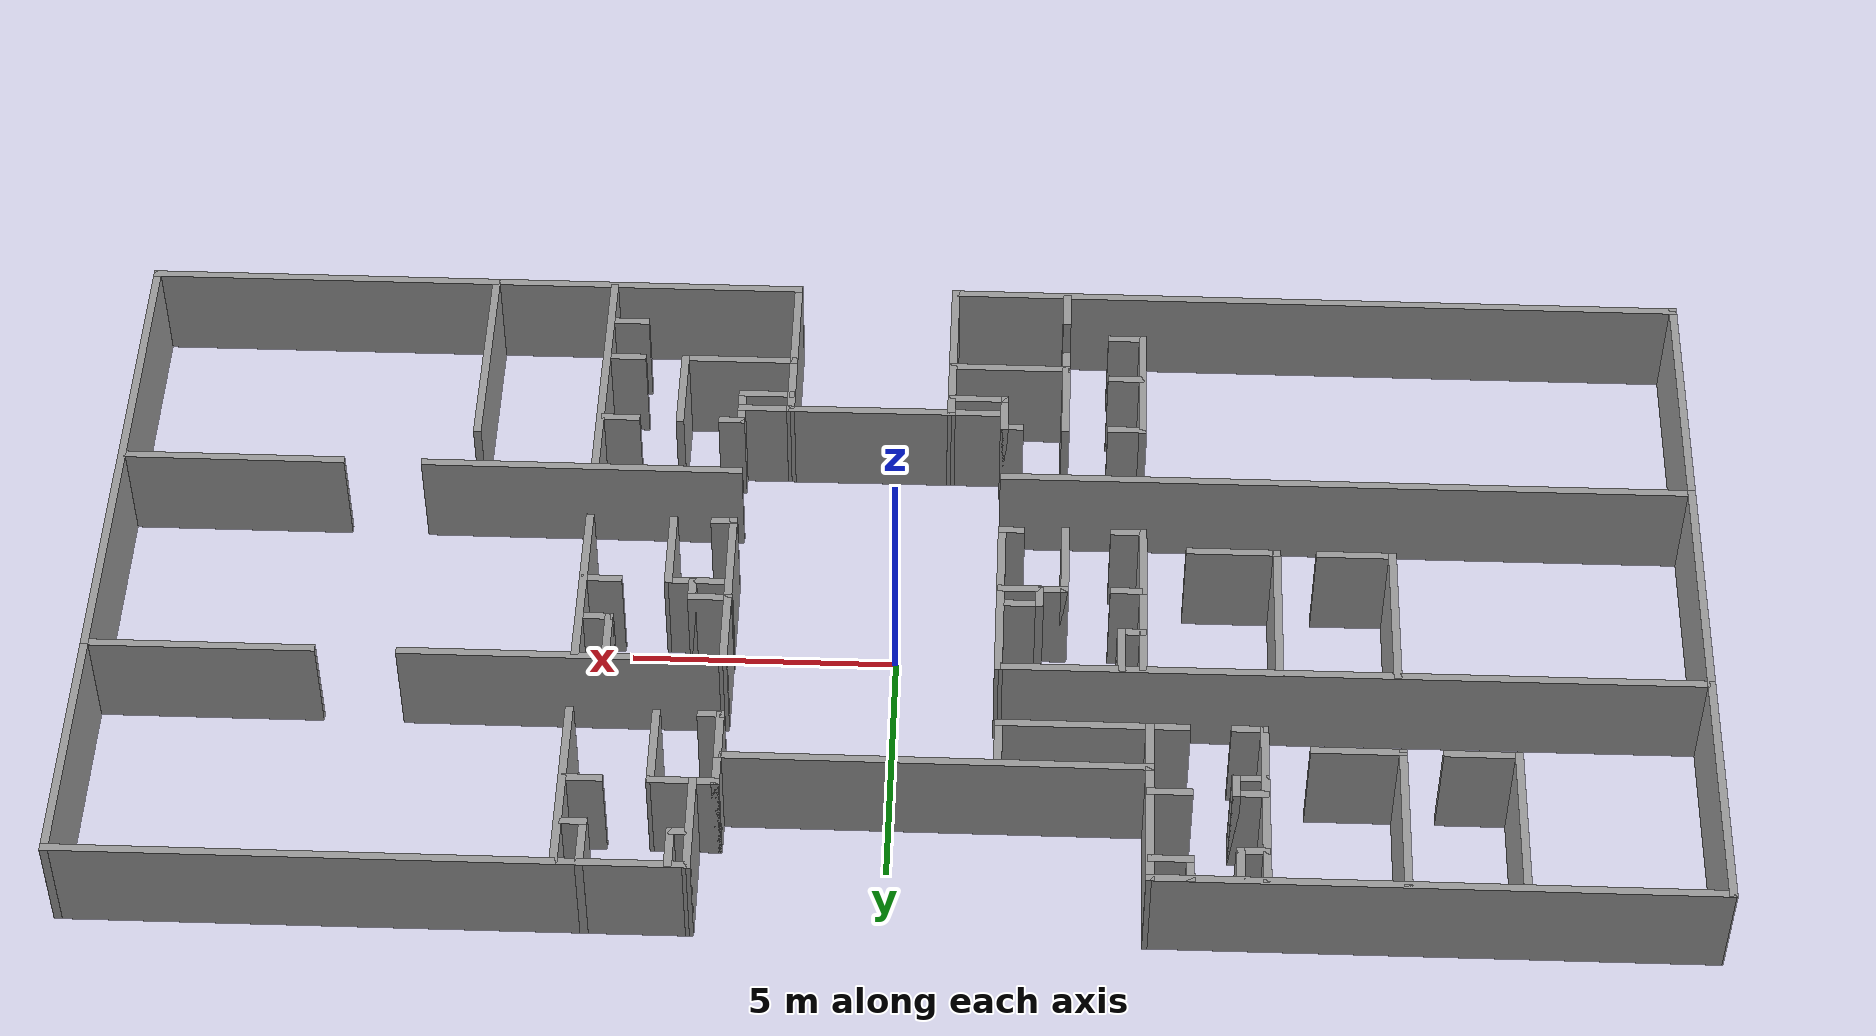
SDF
<?xml version='1.0'?>
<sdf version='1.7'>
  <model name='HQ'>
    <pose>-0.041318 -0.56538 0 0 -0 0</pose>
    <link name='Wall_1'>
      <collision name='Wall_1_Collision'>
        <geometry>
          <box>
            <size>10.3981 0.15 2.0</size>
          </box>
        </geometry>
        <pose>0 0 1.25 0 -0 0</pose>
      </collision>
      <visual name='Wall_1_Visual'>
        <pose>0 0 1.25 0 -0 0</pose>
        <geometry>
          <box>
            <size>10.3981 0.15 2.0</size>
          </box>
        </geometry>
        <material>
          <script>
            <uri>file://media/materials/scripts/gazebo.material</uri>
            <name>Gazebo/Grey</name>
          </script>
          <ambient>1 1 1 1</ambient>
        </material>
        <meta>
          <layer>0</layer>
        </meta>
      </visual>
      <pose>-9.81185 7.21089 0 0 -0 0.000157</pose>
    </link>
    <link name='Wall_100'>
      <collision name='Wall_100_Collision'>
        <geometry>
          <box>
            <size>0.657 0.15 2.0</size>
          </box>
        </geometry>
        <pose>0 0 1.25 0 -0 0</pose>
      </collision>
      <visual name='Wall_100_Visual'>
        <pose>0 0 1.25 0 -0 0</pose>
        <geometry>
          <box>
            <size>0.657 0.15 2.0</size>
          </box>
        </geometry>
        <material>
          <script>
            <uri>file://media/materials/scripts/gazebo.material</uri>
            <name>Gazebo/Grey</name>
          </script>
          <ambient>1 1 1 1</ambient>
        </material>
        <meta>
          <layer>0</layer>
        </meta>
      </visual>
      <pose>-6.48912 5.25147 0 0 -0 3.14159</pose>
    </link>
    <link name='Wall_102'>
      <collision name='Wall_102_Collision'>
        <geometry>
          <box>
            <size>0.5 0.15 2.0</size>
          </box>
        </geometry>
        <pose>0 0 1.25 0 -0 0</pose>
      </collision>
      <visual name='Wall_102_Visual'>
        <pose>0 0 1.25 0 -0 0</pose>
        <geometry>
          <box>
            <size>0.5 0.15 2.0</size>
          </box>
        </geometry>
        <material>
          <script>
            <uri>file://media/materials/scripts/gazebo.material</uri>
            <name>Gazebo/Grey</name>
          </script>
          <ambient>1 1 1 1</ambient>
        </material>
        <meta>
          <layer>0</layer>
        </meta>
      </visual>
      <pose>-6.23562 5.07647 0 0 -0 -1.5708</pose>
    </link>
    <link name='Wall_103'>
      <collision name='Wall_103_Collision'>
        <geometry>
          <box>
            <size>0.668524 0.15 2.0</size>
          </box>
        </geometry>
        <pose>0 0 1.25 0 -0 0</pose>
      </collision>
      <visual name='Wall_103_Visual'>
        <pose>0 0 1.25 0 -0 0</pose>
        <geometry>
          <box>
            <size>0.668524 0.15 2.0</size>
          </box>
        </geometry>
        <material>
          <script>
            <uri>file://media/materials/scripts/gazebo.material</uri>
            <name>Gazebo/Grey</name>
          </script>
          <ambient>1 1 1 1</ambient>
        </material>
        <meta>
          <layer>0</layer>
        </meta>
      </visual>
      <pose>-6.49487 4.89822 0 0 -0 -3.12906</pose>
    </link>
    <link name='Wall_105'>
      <collision name='Wall_105_Collision'>
        <geometry>
          <box>
            <size>0.61 0.15 2.0</size>
          </box>
        </geometry>
        <pose>0 0 1.25 0 -0 0</pose>
      </collision>
      <visual name='Wall_105_Visual'>
        <pose>0 0 1.25 0 -0 0</pose>
        <geometry>
          <box>
            <size>0.61 0.15 2.0</size>
          </box>
        </geometry>
        <material>
          <script>
            <uri>file://media/materials/scripts/gazebo.material</uri>
            <name>Gazebo/Grey</name>
          </script>
          <ambient>1 1 1 1</ambient>
        </material>
        <meta>
          <layer>0</layer>
        </meta>
      </visual>
      <pose>-6.52412 6.55097 0 0 -0 0</pose>
    </link>
    <link name='Wall_106'>
      <collision name='Wall_106_Collision'>
        <geometry>
          <box>
            <size>0.725115 0.15 2.0</size>
          </box>
        </geometry>
        <pose>0 0 1.25 0 -0 0</pose>
      </collision>
      <visual name='Wall_106_Visual'>
        <pose>0 0 1.25 0 -0 0</pose>
        <geometry>
          <box>
            <size>0.725115 0.15 2.0</size>
          </box>
        </geometry>
        <material>
          <script>
            <uri>file://media/materials/scripts/gazebo.material</uri>
            <name>Gazebo/Grey</name>
          </script>
          <ambient>1 1 1 1</ambient>
        </material>
        <meta>
          <layer>0</layer>
        </meta>
      </visual>
      <pose>-6.29412 6.83847 0 0 -0 1.5708</pose>
    </link>
    <link name='Wall_108'>
      <collision name='Wall_108_Collision'>
        <geometry>
          <box>
            <size>3.14002 0.15 2.0</size>
          </box>
        </geometry>
        <pose>0 0 1.25 0 -0 0</pose>
      </collision>
      <visual name='Wall_108_Visual'>
        <pose>0 0 1.25 0 -0 0</pose>
        <geometry>
          <box>
            <size>3.14002 0.15 2.0</size>
          </box>
        </geometry>
        <material>
          <script>
            <uri>file://media/materials/scripts/gazebo.material</uri>
            <name>Gazebo/Grey</name>
          </script>
          <ambient>1 1 1 1</ambient>
        </material>
        <meta>
          <layer>0</layer>
        </meta>
      </visual>
      <pose>-9.25537 5.68847 0 0 -0 -1.57464</pose>
    </link>
    <link name='Wall_109'>
      <collision name='Wall_109_Collision'>
        <geometry>
          <box>
            <size>1.75 0.15 2.0</size>
          </box>
        </geometry>
        <pose>0 0 1.25 0 -0 0</pose>
      </collision>
      <visual name='Wall_109_Visual'>
        <pose>0 0 1.25 0 -0 0</pose>
        <geometry>
          <box>
            <size>1.75 0.15 2.0</size>
          </box>
        </geometry>
        <material>
          <script>
            <uri>file://media/materials/scripts/gazebo.material</uri>
            <name>Gazebo/Grey</name>
          </script>
          <ambient>1 1 1 1</ambient>
        </material>
        <meta>
          <layer>0</layer>
        </meta>
      </visual>
      <pose>-8.46112 4.19347 0 0 -0 0</pose>
    </link>
    <link name='Wall_113'>
      <collision name='Wall_113_Collision'>
        <geometry>
          <box>
            <size>1.43805 0.15 2.0</size>
          </box>
        </geometry>
        <pose>0 0 1.25 0 -0 0</pose>
      </collision>
      <visual name='Wall_113_Visual'>
        <pose>0 0 1.25 0 -0 0</pose>
        <geometry>
          <box>
            <size>1.43805 0.15 2.0</size>
          </box>
        </geometry>
        <material>
          <script>
            <uri>file://media/materials/scripts/gazebo.material</uri>
            <name>Gazebo/Grey</name>
          </script>
          <ambient>1 1 1 1</ambient>
        </material>
        <meta>
          <layer>0</layer>
        </meta>
      </visual>
      <pose>-10.7101 4.19347 0 0 -0 3.14159</pose>
    </link>
    <link name='Wall_114'>
      <collision name='Wall_114_Collision'>
        <geometry>
          <box>
            <size>3.1515 0.15 2.0</size>
          </box>
        </geometry>
        <pose>0 0 1.25 0 -0 0</pose>
      </collision>
      <visual name='Wall_114_Visual'>
        <pose>0 0 1.25 0 -0 0</pose>
        <geometry>
          <box>
            <size>3.1515 0.15 2.0</size>
          </box>
        </geometry>
        <material>
          <script>
            <uri>file://media/materials/scripts/gazebo.material</uri>
            <name>Gazebo/Grey</name>
          </script>
          <ambient>1 1 1 1</ambient>
        </material>
        <meta>
          <layer>0</layer>
        </meta>
      </visual>
      <pose>-11.3541 5.69422 0 0 -0 1.5708</pose>
    </link>
    <link name='Wall_117'>
      <collision name='Wall_117_Collision'>
        <geometry>
          <box>
            <size>0.875898 0.15 2.0</size>
          </box>
        </geometry>
        <pose>0 0 1.25 0 -0 0</pose>
      </collision>
      <visual name='Wall_117_Visual'>
        <pose>0 0 1.25 0 -0 0</pose>
        <geometry>
          <box>
            <size>0.875898 0.15 2.0</size>
          </box>
        </geometry>
        <material>
          <script>
            <uri>file://media/materials/scripts/gazebo.material</uri>
            <name>Gazebo/Grey</name>
          </script>
          <ambient>1 1 1 1</ambient>
        </material>
        <meta>
          <layer>0</layer>
        </meta>
      </visual>
      <pose>-1.88509 -3.99966 0 0 -0 -1.5708</pose>
    </link>
    <link name='Wall_118'>
      <collision name='Wall_118_Collision'>
        <geometry>
          <box>
            <size>1.1557 0.15 2.0</size>
          </box>
        </geometry>
        <pose>0 0 1.25 0 -0 0</pose>
      </collision>
      <visual name='Wall_118_Visual'>
        <pose>0 0 1.25 0 -0 0</pose>
        <geometry>
          <box>
            <size>1.1557 0.15 2.0</size>
          </box>
        </geometry>
        <material>
          <script>
            <uri>file://media/materials/scripts/gazebo.material</uri>
            <name>Gazebo/Grey</name>
          </script>
          <ambient>1 1 1 1</ambient>
        </material>
        <meta>
          <layer>0</layer>
        </meta>
      </visual>
      <pose>-1.38226 -4.3626 0 0 -0 0</pose>
    </link>
    <link name='Wall_120'>
      <collision name='Wall_120_Collision'>
        <geometry>
          <box>
            <size>1.16116 0.15 2.0</size>
          </box>
        </geometry>
        <pose>0 0 1.25 0 -0 0</pose>
      </collision>
      <visual name='Wall_120_Visual'>
        <pose>0 0 1.25 0 -0 0</pose>
        <geometry>
          <box>
            <size>1.16116 0.15 2.0</size>
          </box>
        </geometry>
        <material>
          <script>
            <uri>file://media/materials/scripts/gazebo.material</uri>
            <name>Gazebo/Grey</name>
          </script>
          <ambient>1 1 1 1</ambient>
        </material>
        <meta>
          <layer>0</layer>
        </meta>
      </visual>
      <pose>-1.36439 -3.98262 0 0 -0 -3.13781</pose>
    </link>
    <link name='Wall_122'>
      <collision name='Wall_122_Collision'>
        <geometry>
          <box>
            <size>2.33526 0.15 2.0</size>
          </box>
        </geometry>
        <pose>0 0 1.25 0 -0 0</pose>
      </collision>
      <visual name='Wall_122_Visual'>
        <pose>0 0 1.25 0 -0 0</pose>
        <geometry>
          <box>
            <size>2.33526 0.15 2.0</size>
          </box>
        </geometry>
        <material>
          <script>
            <uri>file://media/materials/scripts/gazebo.material</uri>
            <name>Gazebo/Grey</name>
          </script>
          <ambient>1 1 1 1</ambient>
        </material>
        <meta>
          <layer>0</layer>
        </meta>
      </visual>
      <pose>-1.97205 -5.21705 0 0 -0 3.14159</pose>
    </link>
    <link name='Wall_126'>
      <collision name='Wall_126_Collision'>
        <geometry>
          <box>
            <size>1.73034 0.15 2.0</size>
          </box>
        </geometry>
        <pose>0 0 1.25 0 -0 0</pose>
      </collision>
      <visual name='Wall_126_Visual'>
        <pose>0 0 1.25 0 -0 0</pose>
        <geometry>
          <box>
            <size>1.73034 0.15 2.0</size>
          </box>
        </geometry>
        <material>
          <script>
            <uri>file://media/materials/scripts/gazebo.material</uri>
            <name>Gazebo/Grey</name>
          </script>
          <ambient>1 1 1 1</ambient>
        </material>
        <meta>
          <layer>0</layer>
        </meta>
      </visual>
      <pose>-3.06468 -4.42688 0 0 -0 -1.5708</pose>
    </link>
    <link name='Wall_128'>
      <collision name='Wall_128_Collision'>
        <geometry>
          <box>
            <size>0.444896 0.15 2.0</size>
          </box>
        </geometry>
        <pose>0 0 1.25 0 -0 0</pose>
      </collision>
      <visual name='Wall_128_Visual'>
        <pose>0 0 1.25 0 -0 0</pose>
        <geometry>
          <box>
            <size>0.444896 0.15 2.0</size>
          </box>
        </geometry>
        <material>
          <script>
            <uri>file://media/materials/scripts/gazebo.material</uri>
            <name>Gazebo/Grey</name>
          </script>
          <ambient>1 1 1 1</ambient>
        </material>
        <meta>
          <layer>0</layer>
        </meta>
      </visual>
      <pose>-2.03254 -3.63671 0 0 -0 3.14159</pose>
    </link>
    <link name='Wall_13'>
      <collision name='Wall_13_Collision'>
        <geometry>
          <box>
            <size>4.99102 0.15 2.0</size>
          </box>
        </geometry>
        <pose>0 0 1.25 0 -0 0</pose>
      </collision>
      <visual name='Wall_13_Visual'>
        <pose>0 0 1.25 0 -0 0</pose>
        <geometry>
          <box>
            <size>4.99102 0.15 2.0</size>
          </box>
        </geometry>
        <material>
          <script>
            <uri>file://media/materials/scripts/gazebo.material</uri>
            <name>Gazebo/Grey</name>
          </script>
          <ambient>1 1 1 1</ambient>
        </material>
        <meta>
          <layer>0</layer>
        </meta>
      </visual>
      <pose>14.9584 4.80245 0 0 -0 -1.5696</pose>
    </link>
    <link name='Wall_130'>
      <collision name='Wall_130_Collision'>
        <geometry>
          <box>
            <size>0.535707 0.15 2.0</size>
          </box>
        </geometry>
        <pose>0 0 1.25 0 -0 0</pose>
      </collision>
      <visual name='Wall_130_Visual'>
        <pose>0 0 1.25 0 -0 0</pose>
        <geometry>
          <box>
            <size>0.535707 0.15 2.0</size>
          </box>
        </geometry>
        <material>
          <script>
            <uri>file://media/materials/scripts/gazebo.material</uri>
            <name>Gazebo/Grey</name>
          </script>
          <ambient>1 1 1 1</ambient>
        </material>
        <meta>
          <layer>0</layer>
        </meta>
      </visual>
      <pose>-3.06468 -5.40986 0 0 -0 -1.5708</pose>
    </link>
    <link name='Wall_134'>
      <collision name='Wall_134_Collision'>
        <geometry>
          <box>
            <size>0.800328 0.15 2.0</size>
          </box>
        </geometry>
        <pose>0 0 1.25 0 -0 0</pose>
      </collision>
      <visual name='Wall_134_Visual'>
        <pose>0 0 1.25 0 -0 0</pose>
        <geometry>
          <box>
            <size>0.800328 0.15 2.0</size>
          </box>
        </geometry>
        <material>
          <script>
            <uri>file://media/materials/scripts/gazebo.material</uri>
            <name>Gazebo/Grey</name>
          </script>
          <ambient>1 1 1 1</ambient>
        </material>
        <meta>
          <layer>0</layer>
        </meta>
      </visual>
      <pose>-3.06468 -6.85032 0 0 -0 1.5708</pose>
    </link>
    <link name='Wall_139'>
      <collision name='Wall_139_Collision'>
        <geometry>
          <box>
            <size>6.13288 0.15 2.0</size>
          </box>
        </geometry>
        <pose>0 0 1.25 0 -0 0</pose>
      </collision>
      <visual name='Wall_139_Visual'>
        <pose>0 0 1.25 0 -0 0</pose>
        <geometry>
          <box>
            <size>6.13288 0.15 2.0</size>
          </box>
        </geometry>
        <material>
          <script>
            <uri>file://media/materials/scripts/gazebo.material</uri>
            <name>Gazebo/Grey</name>
          </script>
          <ambient>1 1 1 1</ambient>
        </material>
        <meta>
          <layer>0</layer>
        </meta>
      </visual>
      <pose>6.14807 -2.32093 0 0 -0 -0.001582</pose>
    </link>
    <link name='Wall_142'>
      <collision name='Wall_142_Collision'>
        <geometry>
          <box>
            <size>4.0945 0.15 2.0</size>
          </box>
        </geometry>
        <pose>0 0 1.25 0 -0 0</pose>
      </collision>
      <visual name='Wall_142_Visual'>
        <pose>0 0 1.25 0 -0 0</pose>
        <geometry>
          <box>
            <size>4.0945 0.15 2.0</size>
          </box>
        </geometry>
        <material>
          <script>
            <uri>file://media/materials/scripts/gazebo.material</uri>
            <name>Gazebo/Grey</name>
          </script>
          <ambient>1 1 1 1</ambient>
        </material>
        <meta>
          <layer>0</layer>
        </meta>
      </visual>
      <pose>8.22923 -5.21005 0 0 -0 1.5708</pose>
    </link>
    <link name='Wall_144'>
      <collision name='Wall_144_Collision'>
        <geometry>
          <box>
            <size>4.91701 0.15 2.0</size>
          </box>
        </geometry>
        <pose>0 0 1.25 0 -0 0</pose>
      </collision>
      <visual name='Wall_144_Visual'>
        <pose>0 0 1.25 0 -0 0</pose>
        <geometry>
          <box>
            <size>4.91701 0.15 2.0</size>
          </box>
        </geometry>
        <material>
          <script>
            <uri>file://media/materials/scripts/gazebo.material</uri>
            <name>Gazebo/Grey</name>
          </script>
          <ambient>1 1 1 1</ambient>
        </material>
        <meta>
          <layer>0</layer>
        </meta>
      </visual>
      <pose>5.88898 -4.76429 0 0 -0 1.56838</pose>
    </link>
    <link name='Wall_148'>
      <collision name='Wall_148_Collision'>
        <geometry>
          <box>
            <size>0.75 0.15 2.0</size>
          </box>
        </geometry>
        <pose>0 0 1.25 0 -0 0</pose>
      </collision>
      <visual name='Wall_148_Visual'>
        <pose>0 0 1.25 0 -0 0</pose>
        <geometry>
          <box>
            <size>0.75 0.15 2.0</size>
          </box>
        </geometry>
        <material>
          <script>
            <uri>file://media/materials/scripts/gazebo.material</uri>
            <name>Gazebo/Grey</name>
          </script>
          <ambient>1 1 1 1</ambient>
        </material>
        <meta>
          <layer>0</layer>
        </meta>
      </visual>
      <pose>5.5052 -3.63375 0 0 -0 0</pose>
    </link>
    <link name='Wall_15'>
      <collision name='Wall_15_Collision'>
        <geometry>
          <box>
            <size>9.75 0.15 2.0</size>
          </box>
        </geometry>
        <pose>0 0 1.25 0 -0 0</pose>
      </collision>
      <visual name='Wall_15_Visual'>
        <pose>0 0 1.25 0 -0 0</pose>
        <geometry>
          <box>
            <size>9.75 0.15 2.0</size>
          </box>
        </geometry>
        <material>
          <script>
            <uri>file://media/materials/scripts/gazebo.material</uri>
            <name>Gazebo/Grey</name>
          </script>
          <ambient>1 1 1 1</ambient>
        </material>
        <meta>
          <layer>0</layer>
        </meta>
      </visual>
      <pose>14.9613 -2.41798 0 0 -0 -1.5708</pose>
    </link>
    <link name='Wall_154'>
      <collision name='Wall_154_Collision'>
        <geometry>
          <box>
            <size>0.751903 0.15 2.0</size>
          </box>
        </geometry>
        <pose>0 0 1.25 0 -0 0</pose>
      </collision>
      <visual name='Wall_154_Visual'>
        <pose>0 0 1.25 0 -0 0</pose>
        <geometry>
          <box>
            <size>0.751903 0.15 2.0</size>
          </box>
        </geometry>
        <material>
          <script>
            <uri>file://media/materials/scripts/gazebo.material</uri>
            <name>Gazebo/Grey</name>
          </script>
          <ambient>1 1 1 1</ambient>
        </material>
        <meta>
          <layer>0</layer>
        </meta>
      </visual>
      <pose>5.50425 -5.26133 0 0 -0 0.000815</pose>
    </link>
    <link name='Wall_159'>
      <collision name='Wall_159_Collision'>
        <geometry>
          <box>
            <size>0.800077 0.15 2.0</size>
          </box>
        </geometry>
        <pose>0 0 1.25 0 -0 0</pose>
      </collision>
      <visual name='Wall_159_Visual'>
        <pose>0 0 1.25 0 -0 0</pose>
        <geometry>
          <box>
            <size>0.800077 0.15 2.0</size>
          </box>
        </geometry>
        <material>
          <script>
            <uri>file://media/materials/scripts/gazebo.material</uri>
            <name>Gazebo/Grey</name>
          </script>
          <ambient>1 1 1 1</ambient>
        </material>
        <meta>
          <layer>0</layer>
        </meta>
      </visual>
      <pose>5.53554 -6.23041 0 0 -0 3.14159</pose>
    </link>
    <link name='Wall_163'>
      <collision name='Wall_163_Collision'>
        <geometry>
          <box>
            <size>4.32225 0.15 2.0</size>
          </box>
        </geometry>
        <pose>0 0 1.25 0 -0 0</pose>
      </collision>
      <visual name='Wall_163_Visual'>
        <pose>0 0 1.25 0 -0 0</pose>
        <geometry>
          <box>
            <size>4.32225 0.15 2.0</size>
          </box>
        </geometry>
        <material>
          <script>
            <uri>file://media/materials/scripts/gazebo.material</uri>
            <name>Gazebo/Grey</name>
          </script>
          <ambient>1 1 1 1</ambient>
        </material>
        <meta>
          <layer>0</layer>
        </meta>
      </visual>
      <pose>12.8544 -2.32786 0 0 -0 -0.00122</pose>
    </link>
    <link name='Wall_17'>
      <collision name='Wall_17_Collision'>
        <geometry>
          <box>
            <size>12.8702 0.15 2.0</size>
          </box>
        </geometry>
        <pose>0 0 1.25 0 -0 0</pose>
      </collision>
      <visual name='Wall_17_Visual'>
        <pose>0 0 1.25 0 -0 0</pose>
        <geometry>
          <box>
            <size>12.8702 0.15 2.0</size>
          </box>
        </geometry>
        <material>
          <script>
            <uri>file://media/materials/scripts/gazebo.material</uri>
            <name>Gazebo/Grey</name>
          </script>
          <ambient>1 1 1 1</ambient>
        </material>
        <meta>
          <layer>0</layer>
        </meta>
      </visual>
      <pose>8.60126 -7.2205 0 0 -0 -3.1412</pose>
    </link>
    <link name='Wall_171'>
      <collision name='Wall_171_Collision'>
        <geometry>
          <box>
            <size>3.58693 0.15 2.0</size>
          </box>
        </geometry>
        <pose>0 0 1.25 0 -0 0</pose>
      </collision>
      <visual name='Wall_171_Visual'>
        <pose>0 0 1.25 0 -0 0</pose>
        <geometry>
          <box>
            <size>3.58693 0.15 2.0</size>
          </box>
        </geometry>
        <material>
          <script>
            <uri>file://media/materials/scripts/gazebo.material</uri>
            <name>Gazebo/Grey</name>
          </script>
          <ambient>1 1 1 1</ambient>
        </material>
        <meta>
          <layer>0</layer>
        </meta>
      </visual>
      <pose>3.16808 0.700941 0 0 -0 1.57282</pose>
    </link>
    <link name='Wall_177'>
      <collision name='Wall_177_Collision'>
        <geometry>
          <box>
            <size>6.10576 0.15 2.0</size>
          </box>
        </geometry>
        <pose>0 0 1.25 0 -0 0</pose>
      </collision>
      <visual name='Wall_177_Visual'>
        <pose>0 0 1.25 0 -0 0</pose>
        <geometry>
          <box>
            <size>6.10576 0.15 2.0</size>
          </box>
        </geometry>
        <material>
          <script>
            <uri>file://media/materials/scripts/gazebo.material</uri>
            <name>Gazebo/Grey</name>
          </script>
          <ambient>1 1 1 1</ambient>
        </material>
        <meta>
          <layer>0</layer>
        </meta>
      </visual>
      <pose>6.14231 2.4172 0 0 -0 -0.00074</pose>
    </link>
    <link name='Wall_18'>
      <collision name='Wall_18_Collision'>
        <geometry>
          <box>
            <size>3.40471 0.15 2.0</size>
          </box>
        </geometry>
        <pose>0 0 1.25 0 -0 0</pose>
      </collision>
      <visual name='Wall_18_Visual'>
        <pose>0 0 1.25 0 -0 0</pose>
        <geometry>
          <box>
            <size>3.40471 0.15 2.0</size>
          </box>
        </geometry>
        <material>
          <script>
            <uri>file://media/materials/scripts/gazebo.material</uri>
            <name>Gazebo/Grey</name>
          </script>
          <ambient>1 1 1 1</ambient>
        </material>
        <meta>
          <layer>0</layer>
        </meta>
      </visual>
      <pose>2.24118 -5.59568 0 0 -0 1.5708</pose>
    </link>
    <link name='Wall_182'>
      <collision name='Wall_182_Collision'>
        <geometry>
          <box>
            <size>4.34 0.15 2.0</size>
          </box>
        </geometry>
        <pose>0 0 1.25 0 -0 0</pose>
      </collision>
      <visual name='Wall_182_Visual'>
        <pose>0 0 1.25 0 -0 0</pose>
        <geometry>
          <box>
            <size>4.34 0.15 2.0</size>
          </box>
        </geometry>
        <material>
          <script>
            <uri>file://media/materials/scripts/gazebo.material</uri>
            <name>Gazebo/Grey</name>
          </script>
          <ambient>1 1 1 1</ambient>
        </material>
        <meta>
          <layer>0</layer>
        </meta>
      </visual>
      <pose>12.865 2.415 0 0 -0 0</pose>
    </link>
    <link name='Wall_187'>
      <collision name='Wall_187_Collision'>
        <geometry>
          <box>
            <size>3.48674 0.15 2.0</size>
          </box>
        </geometry>
        <pose>0 0 1.25 0 -0 0</pose>
      </collision>
      <visual name='Wall_187_Visual'>
        <pose>0 0 1.25 0 -0 0</pose>
        <geometry>
          <box>
            <size>3.48674 0.15 2.0</size>
          </box>
        </geometry>
        <material>
          <script>
            <uri>file://media/materials/scripts/gazebo.material</uri>
            <name>Gazebo/Grey</name>
          </script>
          <ambient>1 1 1 1</ambient>
        </material>
        <meta>
          <layer>0</layer>
        </meta>
      </visual>
      <pose>5.89015 0.650841 0 0 -0 1.56805</pose>
    </link>
    <link name='Wall_19'>
      <collision name='Wall_19_Collision'>
        <geometry>
          <box>
            <size>1.09306 0.15 2.0</size>
          </box>
        </geometry>
        <pose>0 0 1.25 0 -0 0</pose>
      </collision>
      <visual name='Wall_19_Visual'>
        <pose>0 0 1.25 0 -0 0</pose>
        <geometry>
          <box>
            <size>1.09306 0.15 2.0</size>
          </box>
        </geometry>
        <material>
          <script>
            <uri>file://media/materials/scripts/gazebo.material</uri>
            <name>Gazebo/Grey</name>
          </script>
          <ambient>1 1 1 1</ambient>
        </material>
        <meta>
          <layer>0</layer>
        </meta>
      </visual>
      <pose>2.71265 -3.96834 0 0 -0 0</pose>
    </link>
    <link name='Wall_192'>
      <collision name='Wall_192_Collision'>
        <geometry>
          <box>
            <size>0.5 0.15 2.0</size>
          </box>
        </geometry>
        <pose>0 0 1.25 0 -0 0</pose>
      </collision>
      <visual name='Wall_192_Visual'>
        <pose>0 0 1.25 0 -0 0</pose>
        <geometry>
          <box>
            <size>0.5 0.15 2.0</size>
          </box>
        </geometry>
        <material>
          <script>
            <uri>file://media/materials/scripts/gazebo.material</uri>
            <name>Gazebo/Grey</name>
          </script>
          <ambient>1 1 1 1</ambient>
        </material>
        <meta>
          <layer>0</layer>
        </meta>
      </visual>
      <pose>3.34656 -1.01752 0 0 -0 0</pose>
    </link>
    <link name='Wall_198'>
      <collision name='Wall_198_Collision'>
        <geometry>
          <box>
            <size>1.2655 0.15 2.0</size>
          </box>
        </geometry>
        <pose>0 0 1.25 0 -0 0</pose>
      </collision>
      <visual name='Wall_198_Visual'>
        <pose>0 0 1.25 0 -0 0</pose>
        <geometry>
          <box>
            <size>1.2655 0.15 2.0</size>
          </box>
        </geometry>
        <material>
          <script>
            <uri>file://media/materials/scripts/gazebo.material</uri>
            <name>Gazebo/Grey</name>
          </script>
          <ambient>1 1 1 1</ambient>
        </material>
        <meta>
          <layer>0</layer>
        </meta>
      </visual>
      <pose>3.74081 0.511977 0 0 -0 0</pose>
    </link>
    <link name='Wall_20'>
      <collision name='Wall_20_Collision'>
        <geometry>
          <box>
            <size>0.484593 0.15 2.0</size>
          </box>
        </geometry>
        <pose>0 0 1.25 0 -0 0</pose>
      </collision>
      <visual name='Wall_20_Visual'>
        <pose>0 0 1.25 0 -0 0</pose>
        <geometry>
          <box>
            <size>0.484593 0.15 2.0</size>
          </box>
        </geometry>
        <material>
          <script>
            <uri>file://media/materials/scripts/gazebo.material</uri>
            <name>Gazebo/Grey</name>
          </script>
          <ambient>1 1 1 1</ambient>
        </material>
        <meta>
          <layer>0</layer>
        </meta>
      </visual>
      <pose>3.18412 -3.80105 0 0 -0 1.5708</pose>
    </link>
    <link name='Wall_202'>
      <collision name='Wall_202_Collision'>
        <geometry>
          <box>
            <size>1.66652 0.15 2.0</size>
          </box>
        </geometry>
        <pose>0 0 1.25 0 -0 0</pose>
      </collision>
      <visual name='Wall_202_Visual'>
        <pose>0 0 1.25 0 -0 0</pose>
        <geometry>
          <box>
            <size>1.66652 0.15 2.0</size>
          </box>
        </geometry>
        <material>
          <script>
            <uri>file://media/materials/scripts/gazebo.material</uri>
            <name>Gazebo/Grey</name>
          </script>
          <ambient>1 1 1 1</ambient>
        </material>
        <meta>
          <layer>0</layer>
        </meta>
      </visual>
      <pose>4.29995 -0.246283 0 0 -0 -1.56896</pose>
    </link>
    <link name='Wall_204'>
      <collision name='Wall_204_Collision'>
        <geometry>
          <box>
            <size>0.836128 0.15 2.0</size>
          </box>
        </geometry>
        <pose>0 0 1.25 0 -0 0</pose>
      </collision>
      <visual name='Wall_204_Visual'>
        <pose>0 0 1.25 0 -0 0</pose>
        <geometry>
          <box>
            <size>0.836128 0.15 2.0</size>
          </box>
        </geometry>
        <material>
          <script>
            <uri>file://media/materials/scripts/gazebo.material</uri>
            <name>Gazebo/Grey</name>
          </script>
          <ambient>1 1 1 1</ambient>
        </material>
        <meta>
          <layer>0</layer>
        </meta>
      </visual>
      <pose>3.49517 0.905114 0 0 -0 0</pose>
    </link>
    <link name='Wall_205'>
      <collision name='Wall_205_Collision'>
        <geometry>
          <box>
            <size>0.52164 0.15 2.0</size>
          </box>
        </geometry>
        <pose>0 0 1.25 0 -0 0</pose>
      </collision>
      <visual name='Wall_205_Visual'>
        <pose>0 0 1.25 0 -0 0</pose>
        <geometry>
          <box>
            <size>0.52164 0.15 2.0</size>
          </box>
        </geometry>
        <material>
          <script>
            <uri>file://media/materials/scripts/gazebo.material</uri>
            <name>Gazebo/Grey</name>
          </script>
          <ambient>1 1 1 1</ambient>
        </material>
        <meta>
          <layer>0</layer>
        </meta>
      </visual>
      <pose>3.83822 0.719294 0 0 -0 -1.5708</pose>
    </link>
    <link name='Wall_209'>
      <collision name='Wall_209_Collision'>
        <geometry>
          <box>
            <size>0.761883 0.15 2.0</size>
          </box>
        </geometry>
        <pose>0 0 1.25 0 -0 0</pose>
      </collision>
      <visual name='Wall_209_Visual'>
        <pose>0 0 1.25 0 -0 0</pose>
        <geometry>
          <box>
            <size>0.761883 0.15 2.0</size>
          </box>
        </geometry>
        <material>
          <script>
            <uri>file://media/materials/scripts/gazebo.material</uri>
            <name>Gazebo/Grey</name>
          </script>
          <ambient>1 1 1 1</ambient>
        </material>
        <meta>
          <layer>0</layer>
        </meta>
      </visual>
      <pose>5.5449 0.510604 0 0 -0 0</pose>
    </link>
    <link name='Wall_213'>
      <collision name='Wall_213_Collision'>
        <geometry>
          <box>
            <size>3.64548 0.15 2.0</size>
          </box>
        </geometry>
        <pose>0 0 1.25 0 -0 0</pose>
      </collision>
      <visual name='Wall_213_Visual'>
        <pose>0 0 1.25 0 -0 0</pose>
        <geometry>
          <box>
            <size>3.64548 0.15 2.0</size>
          </box>
        </geometry>
        <material>
          <script>
            <uri>file://media/materials/scripts/gazebo.material</uri>
            <name>Gazebo/Grey</name>
          </script>
          <ambient>1 1 1 1</ambient>
        </material>
        <meta>
          <layer>0</layer>
        </meta>
      </visual>
      <pose>5.88933 5.46612 0 0 -0 1.57131</pose>
    </link>
    <link name='Wall_217'>
      <collision name='Wall_217_Collision'>
        <geometry>
          <box>
            <size>1.10451 0.15 2.0</size>
          </box>
        </geometry>
        <pose>0 0 1.25 0 -0 0</pose>
      </collision>
      <visual name='Wall_217_Visual'>
        <pose>0 0 1.25 0 -0 0</pose>
        <geometry>
          <box>
            <size>1.10451 0.15 2.0</size>
          </box>
        </geometry>
        <material>
          <script>
            <uri>file://media/materials/scripts/gazebo.material</uri>
            <name>Gazebo/Grey</name>
          </script>
          <ambient>1 1 1 1</ambient>
        </material>
        <meta>
          <layer>0</layer>
        </meta>
      </visual>
      <pose>3.12789 4.20563 0 0 -0 -1.56588</pose>
    </link>
    <link name='Wall_22'>
      <collision name='Wall_22_Collision'>
        <geometry>
          <box>
            <size>1.77741 0.15 2.0</size>
          </box>
        </geometry>
        <pose>0 0 1.25 0 -0 0</pose>
      </collision>
      <visual name='Wall_22_Visual'>
        <pose>0 0 1.25 0 -0 0</pose>
        <geometry>
          <box>
            <size>1.77741 0.15 2.0</size>
          </box>
        </geometry>
        <material>
          <script>
            <uri>file://media/materials/scripts/gazebo.material</uri>
            <name>Gazebo/Grey</name>
          </script>
          <ambient>1 1 1 1</ambient>
        </material>
        <meta>
          <layer>0</layer>
        </meta>
      </visual>
      <pose>4.3552 -4.44742 0 0 -0 -1.5708</pose>
    </link>
    <link name='Wall_220'>
      <collision name='Wall_220_Collision'>
        <geometry>
          <box>
            <size>0.5 0.15 2.0</size>
          </box>
        </geometry>
        <pose>0 0 1.25 0 -0 0</pose>
      </collision>
      <visual name='Wall_220_Visual'>
        <pose>0 0 1.25 0 -0 0</pose>
        <geometry>
          <box>
            <size>0.5 0.15 2.0</size>
          </box>
        </geometry>
        <material>
          <script>
            <uri>file://media/materials/scripts/gazebo.material</uri>
            <name>Gazebo/Grey</name>
          </script>
          <ambient>1 1 1 1</ambient>
        </material>
        <meta>
          <layer>0</layer>
        </meta>
      </visual>
      <pose>3.30523 3.72838 0 0 -0 0</pose>
    </link>
    <link name='Wall_222'>
      <collision name='Wall_222_Collision'>
        <geometry>
          <box>
            <size>1.71003 0.15 2.0</size>
          </box>
        </geometry>
        <pose>0 0 1.25 0 -0 0</pose>
      </collision>
      <visual name='Wall_222_Visual'>
        <pose>0 0 1.25 0 -0 0</pose>
        <geometry>
          <box>
            <size>1.71003 0.15 2.0</size>
          </box>
        </geometry>
        <material>
          <script>
            <uri>file://media/materials/scripts/gazebo.material</uri>
            <name>Gazebo/Grey</name>
          </script>
          <ambient>1 1 1 1</ambient>
        </material>
        <meta>
          <layer>0</layer>
        </meta>
      </visual>
      <pose>4.30023 4.51838 0 0 -0 1.5708</pose>
    </link>
    <link name='Wall_224'>
      <collision name='Wall_224_Collision'>
        <geometry>
          <box>
            <size>0.914701 0.15 2.0</size>
          </box>
        </geometry>
        <pose>0 0 1.25 0 -0 0</pose>
      </collision>
      <visual name='Wall_224_Visual'>
        <pose>0 0 1.25 0 -0 0</pose>
        <geometry>
          <box>
            <size>0.914701 0.15 2.0</size>
          </box>
        </geometry>
        <material>
          <script>
            <uri>file://media/materials/scripts/gazebo.material</uri>
            <name>Gazebo/Grey</name>
          </script>
          <ambient>1 1 1 1</ambient>
        </material>
        <meta>
          <layer>0</layer>
        </meta>
      </visual>
      <pose>3.91789 5.30063 0 0 -0 -0.005876</pose>
    </link>
    <link name='Wall_23'>
      <collision name='Wall_23_Collision'>
        <geometry>
          <box>
            <size>2.25 0.15 2.0</size>
          </box>
        </geometry>
        <pose>0 0 1.25 0 -0 0</pose>
      </collision>
      <visual name='Wall_23_Visual'>
        <pose>0 0 1.25 0 -0 0</pose>
        <geometry>
          <box>
            <size>2.25 0.15 2.0</size>
          </box>
        </geometry>
        <material>
          <script>
            <uri>file://media/materials/scripts/gazebo.material</uri>
            <name>Gazebo/Grey</name>
          </script>
          <ambient>1 1 1 1</ambient>
        </material>
        <meta>
          <layer>0</layer>
        </meta>
      </visual>
      <pose>3.3052 -5.26109 0 0 -0 3.14159</pose>
    </link>
    <link name='Wall_230'>
      <collision name='Wall_230_Collision'>
        <geometry>
          <box>
            <size>0.75 0.15 2.0</size>
          </box>
        </geometry>
        <pose>0 0 1.25 0 -0 0</pose>
      </collision>
      <visual name='Wall_230_Visual'>
        <pose>0 0 1.25 0 -0 0</pose>
        <geometry>
          <box>
            <size>0.75 0.15 2.0</size>
          </box>
        </geometry>
        <material>
          <script>
            <uri>file://media/materials/scripts/gazebo.material</uri>
            <name>Gazebo/Grey</name>
          </script>
          <ambient>1 1 1 1</ambient>
        </material>
        <meta>
          <layer>0</layer>
        </meta>
      </visual>
      <pose>5.53023 5.29838 0 0 -0 0</pose>
    </link>
    <link name='Wall_232'>
      <collision name='Wall_232_Collision'>
        <geometry>
          <box>
            <size>1.07 0.15 2.0</size>
          </box>
        </geometry>
        <pose>0 0 1.25 0 -0 0</pose>
      </collision>
      <visual name='Wall_232_Visual'>
        <pose>0 0 1.25 0 -0 0</pose>
        <geometry>
          <box>
            <size>1.07 0.15 2.0</size>
          </box>
        </geometry>
        <material>
          <script>
            <uri>file://media/materials/scripts/gazebo.material</uri>
            <name>Gazebo/Grey</name>
          </script>
          <ambient>1 1 1 1</ambient>
        </material>
        <meta>
          <layer>0</layer>
        </meta>
      </visual>
      <pose>5.43023 6.75838 0 0 -0 -1.5708</pose>
    </link>
    <link name='Wall_233'>
      <collision name='Wall_233_Collision'>
        <geometry>
          <box>
            <size>0.5 0.15 2.0</size>
          </box>
        </geometry>
        <pose>0 0 1.25 0 -0 0</pose>
      </collision>
      <visual name='Wall_233_Visual'>
        <pose>0 0 1.25 0 -0 0</pose>
        <geometry>
          <box>
            <size>0.5 0.15 2.0</size>
          </box>
        </geometry>
        <material>
          <script>
            <uri>file://media/materials/scripts/gazebo.material</uri>
            <name>Gazebo/Grey</name>
          </script>
          <ambient>1 1 1 1</ambient>
        </material>
        <meta>
          <layer>0</layer>
        </meta>
      </visual>
      <pose>5.60523 6.29838 0 0 -0 0</pose>
    </link>
    <link name='Wall_235'>
      <collision name='Wall_235_Collision'>
        <geometry>
          <box>
            <size>0.5 0.15 2.0</size>
          </box>
        </geometry>
        <pose>0 0 1.25 0 -0 0</pose>
      </collision>
      <visual name='Wall_235_Visual'>
        <pose>0 0 1.25 0 -0 0</pose>
        <geometry>
          <box>
            <size>0.5 0.15 2.0</size>
          </box>
        </geometry>
        <material>
          <script>
            <uri>file://media/materials/scripts/gazebo.material</uri>
            <name>Gazebo/Grey</name>
          </script>
          <ambient>1 1 1 1</ambient>
        </material>
        <meta>
          <layer>0</layer>
        </meta>
      </visual>
      <pose>3.35912 -3.63375 0 0 -0 0</pose>
    </link>
    <link name='Wall_237'>
      <collision name='Wall_237_Collision'>
        <geometry>
          <box>
            <size>0.584783 0.15 2.0</size>
          </box>
        </geometry>
        <pose>0 0 1.25 0 -0 0</pose>
      </collision>
      <visual name='Wall_237_Visual'>
        <pose>0 0 1.25 0 -0 0</pose>
        <geometry>
          <box>
            <size>0.584783 0.15 2.0</size>
          </box>
        </geometry>
        <material>
          <script>
            <uri>file://media/materials/scripts/gazebo.material</uri>
            <name>Gazebo/Grey</name>
          </script>
          <ambient>1 1 1 1</ambient>
        </material>
        <meta>
          <layer>0</layer>
        </meta>
      </visual>
      <pose>-5.40371 6.99084 0 0 -0 -1.5708</pose>
    </link>
    <link name='Wall_238'>
      <collision name='Wall_238_Collision'>
        <geometry>
          <box>
            <size>0.84587 0.15 2.0</size>
          </box>
        </geometry>
        <pose>0 0 1.25 0 -0 0</pose>
      </collision>
      <visual name='Wall_238_Visual'>
        <pose>0 0 1.25 0 -0 0</pose>
        <geometry>
          <box>
            <size>0.84587 0.15 2.0</size>
          </box>
        </geometry>
        <material>
          <script>
            <uri>file://media/materials/scripts/gazebo.material</uri>
            <name>Gazebo/Grey</name>
          </script>
          <ambient>1 1 1 1</ambient>
        </material>
        <meta>
          <layer>0</layer>
        </meta>
      </visual>
      <pose>-5.05589 6.77345 0 0 -0 0</pose>
    </link>
    <link name='Wall_240'>
      <collision name='Wall_240_Collision'>
        <geometry>
          <box>
            <size>0.490265 0.15 2.0</size>
          </box>
        </geometry>
        <pose>0 0 1.25 0 -0 0</pose>
      </collision>
      <visual name='Wall_240_Visual'>
        <pose>0 0 1.25 0 -0 0</pose>
        <geometry>
          <box>
            <size>0.490265 0.15 2.0</size>
          </box>
        </geometry>
        <material>
          <script>
            <uri>file://media/materials/scripts/gazebo.material</uri>
            <name>Gazebo/Grey</name>
          </script>
          <ambient>1 1 1 1</ambient>
        </material>
        <meta>
          <layer>0</layer>
        </meta>
      </visual>
      <pose>-2.6327 0.685901 0 0 -0 1.5708</pose>
    </link>
    <link name='Wall_241'>
      <collision name='Wall_241_Collision'>
        <geometry>
          <box>
            <size>0.75 0.15 2.0</size>
          </box>
        </geometry>
        <pose>0 0 1.25 0 -0 0</pose>
      </collision>
      <visual name='Wall_241_Visual'>
        <pose>0 0 1.25 0 -0 0</pose>
        <geometry>
          <box>
            <size>0.75 0.15 2.0</size>
          </box>
        </geometry>
        <material>
          <script>
            <uri>file://media/materials/scripts/gazebo.material</uri>
            <name>Gazebo/Grey</name>
          </script>
          <ambient>1 1 1 1</ambient>
        </material>
        <meta>
          <layer>0</layer>
        </meta>
      </visual>
      <pose>-2.3327 0.856033 0 0 -0 0</pose>
    </link>
    <link name='Wall_244'>
      <collision name='Wall_244_Collision'>
        <geometry>
          <box>
            <size>0.75 0.15 2.0</size>
          </box>
        </geometry>
        <pose>0 0 1.25 0 -0 0</pose>
      </collision>
      <visual name='Wall_244_Visual'>
        <pose>0 0 1.25 0 -0 0</pose>
        <geometry>
          <box>
            <size>0.75 0.15 2.0</size>
          </box>
        </geometry>
        <material>
          <script>
            <uri>file://media/materials/scripts/gazebo.material</uri>
            <name>Gazebo/Grey</name>
          </script>
          <ambient>1 1 1 1</ambient>
        </material>
        <meta>
          <layer>0</layer>
        </meta>
      </visual>
      <pose>-4.25062 -3.64086 0 0 -0 3.14159</pose>
    </link>
    <link name='Wall_247'>
      <collision name='Wall_247_Collision'>
        <geometry>
          <box>
            <size>2.58803 0.15 2.0</size>
          </box>
        </geometry>
        <pose>0 0 1.25 0 -0 0</pose>
      </collision>
      <visual name='Wall_247_Visual'>
        <pose>0 0 1.25 0 -0 0</pose>
        <geometry>
          <box>
            <size>2.58803 0.15 2.0</size>
          </box>
        </geometry>
        <material>
          <script>
            <uri>file://media/materials/scripts/gazebo.material</uri>
            <name>Gazebo/Grey</name>
          </script>
          <ambient>1 1 1 1</ambient>
        </material>
        <meta>
          <layer>0</layer>
        </meta>
      </visual>
      <pose>-4.55062 -4.85987 0 0 -0 -1.5708</pose>
    </link>
    <link name='Wall_25'>
      <collision name='Wall_25_Collision'>
        <geometry>
          <box>
            <size>3.25 0.15 2.0</size>
          </box>
        </geometry>
        <pose>0 0 1.25 0 -0 0</pose>
      </collision>
      <visual name='Wall_25_Visual'>
        <pose>0 0 1.25 0 -0 0</pose>
        <geometry>
          <box>
            <size>3.25 0.15 2.0</size>
          </box>
        </geometry>
        <material>
          <script>
            <uri>file://media/materials/scripts/gazebo.material</uri>
            <name>Gazebo/Grey</name>
          </script>
          <ambient>1 1 1 1</ambient>
        </material>
        <meta>
          <layer>0</layer>
        </meta>
      </visual>
      <pose>0.691182 -3.97576 0 0 -0 -3.13681</pose>
    </link>
    <link name='Wall_251'>
      <collision name='Wall_251_Collision'>
        <geometry>
          <box>
            <size>0.75 0.15 2.0</size>
          </box>
        </geometry>
        <pose>0 0 1.25 0 -0 0</pose>
      </collision>
      <visual name='Wall_251_Visual'>
        <pose>0 0 1.25 0 -0 0</pose>
        <geometry>
          <box>
            <size>0.75 0.15 2.0</size>
          </box>
        </geometry>
        <material>
          <script>
            <uri>file://media/materials/scripts/gazebo.material</uri>
            <name>Gazebo/Grey</name>
          </script>
          <ambient>1 1 1 1</ambient>
        </material>
        <meta>
          <layer>0</layer>
        </meta>
      </visual>
      <pose>-4.25062 -6.07887 0 0 -0 0</pose>
    </link>
    <link name='Wall_258'>
      <collision name='Wall_258_Collision'>
        <geometry>
          <box>
            <size>0.727018 0.15 2.0</size>
          </box>
        </geometry>
        <pose>0 0 1.25 0 -0 0</pose>
      </collision>
      <visual name='Wall_258_Visual'>
        <pose>0 0 1.25 0 -0 0</pose>
        <geometry>
          <box>
            <size>0.727018 0.15 2.0</size>
          </box>
        </geometry>
        <material>
          <script>
            <uri>file://media/materials/scripts/gazebo.material</uri>
            <name>Gazebo/Grey</name>
          </script>
          <ambient>1 1 1 1</ambient>
        </material>
        <meta>
          <layer>0</layer>
        </meta>
      </visual>
      <pose>-4.23912 -4.98862 0 0 -0 3.13379</pose>
    </link>
    <link name='Wall_26'>
      <collision name='Wall_26_Collision'>
        <geometry>
          <box>
            <size>3.38946 0.15 2.0</size>
          </box>
        </geometry>
        <pose>0 0 1.25 0 -0 0</pose>
      </collision>
      <visual name='Wall_26_Visual'>
        <pose>0 0 1.25 0 -0 0</pose>
        <geometry>
          <box>
            <size>3.38946 0.15 2.0</size>
          </box>
        </geometry>
        <material>
          <script>
            <uri>file://media/materials/scripts/gazebo.material</uri>
            <name>Gazebo/Grey</name>
          </script>
          <ambient>1 1 1 1</ambient>
        </material>
        <meta>
          <layer>0</layer>
        </meta>
      </visual>
      <pose>-0.860111 -5.60044 0 0 -0 -1.57159</pose>
    </link>
    <link name='Wall_260'>
      <collision name='Wall_260_Collision'>
        <geometry>
          <box>
            <size>0.453029 0.15 2.0</size>
          </box>
        </geometry>
        <pose>0 0 1.25 0 -0 0</pose>
      </collision>
      <visual name='Wall_260_Visual'>
        <pose>0 0 1.25 0 -0 0</pose>
        <geometry>
          <box>
            <size>0.453029 0.15 2.0</size>
          </box>
        </geometry>
        <material>
          <script>
            <uri>file://media/materials/scripts/gazebo.material</uri>
            <name>Gazebo/Grey</name>
          </script>
          <ambient>1 1 1 1</ambient>
        </material>
        <meta>
          <layer>0</layer>
        </meta>
      </visual>
      <pose>3.70877 6.46205 0 0 -0 0</pose>
    </link>
    <link name='Wall_261'>
      <collision name='Wall_261_Collision'>
        <geometry>
          <box>
            <size>0.876329 0.15 2.0</size>
          </box>
        </geometry>
        <pose>0 0 1.25 0 -0 0</pose>
      </collision>
      <visual name='Wall_261_Visual'>
        <pose>0 0 1.25 0 -0 0</pose>
        <geometry>
          <box>
            <size>0.876329 0.15 2.0</size>
          </box>
        </geometry>
        <material>
          <script>
            <uri>file://media/materials/scripts/gazebo.material</uri>
            <name>Gazebo/Grey</name>
          </script>
          <ambient>1 1 1 1</ambient>
        </material>
        <meta>
          <layer>0</layer>
        </meta>
      </visual>
      <pose>3.85743 6.82511 0 0 -0 1.57867</pose>
    </link>
    <link name='Wall_265'>
      <collision name='Wall_265_Collision'>
        <geometry>
          <box>
            <size>0.534494 0.15 2.0</size>
          </box>
        </geometry>
        <pose>0 0 1.25 0 -0 0</pose>
      </collision>
      <visual name='Wall_265_Visual'>
        <pose>0 0 1.25 0 -0 0</pose>
        <geometry>
          <box>
            <size>0.534494 0.15 2.0</size>
          </box>
        </geometry>
        <material>
          <script>
            <uri>file://media/materials/scripts/gazebo.material</uri>
            <name>Gazebo/Grey</name>
          </script>
          <ambient>1 1 1 1</ambient>
        </material>
        <meta>
          <layer>0</layer>
        </meta>
      </visual>
      <pose>3.18508 -4.16059 0 0 -0 -1.56585</pose>
    </link>
    <link name='Wall_267'>
      <collision name='Wall_267_Collision'>
        <geometry>
          <box>
            <size>1.07773 0.15 2.0</size>
          </box>
        </geometry>
        <pose>0 0 1.25 0 -0 0</pose>
      </collision>
      <visual name='Wall_267_Visual'>
        <pose>0 0 1.25 0 -0 0</pose>
        <geometry>
          <box>
            <size>1.07773 0.15 2.0</size>
          </box>
        </geometry>
        <material>
          <script>
            <uri>file://media/materials/scripts/gazebo.material</uri>
            <name>Gazebo/Grey</name>
          </script>
          <ambient>1 1 1 1</ambient>
        </material>
        <meta>
          <layer>0</layer>
        </meta>
      </visual>
      <pose>2.72216 -4.35283 0 0 -0 3.14159</pose>
    </link>
    <link name='Wall_269'>
      <collision name='Wall_269_Collision'>
        <geometry>
          <box>
            <size>1.09913 0.15 2.0</size>
          </box>
        </geometry>
        <pose>0 0 1.25 0 -0 0</pose>
      </collision>
      <visual name='Wall_269_Visual'>
        <pose>0 0 1.25 0 -0 0</pose>
        <geometry>
          <box>
            <size>1.09913 0.15 2.0</size>
          </box>
        </geometry>
        <material>
          <script>
            <uri>file://media/materials/scripts/gazebo.material</uri>
            <name>Gazebo/Grey</name>
          </script>
          <ambient>1 1 1 1</ambient>
        </material>
        <meta>
          <layer>0</layer>
        </meta>
      </visual>
      <pose>5.33585 1.92159 0 0 -0 -1.5708</pose>
    </link>
    <link name='Wall_270'>
      <collision name='Wall_270_Collision'>
        <geometry>
          <box>
            <size>0.698883 0.15 2.0</size>
          </box>
        </geometry>
        <pose>0 0 1.25 0 -0 0</pose>
      </collision>
      <visual name='Wall_270_Visual'>
        <pose>0 0 1.25 0 -0 0</pose>
        <geometry>
          <box>
            <size>0.698883 0.15 2.0</size>
          </box>
        </geometry>
        <material>
          <script>
            <uri>file://media/materials/scripts/gazebo.material</uri>
            <name>Gazebo/Grey</name>
          </script>
          <ambient>1 1 1 1</ambient>
        </material>
        <meta>
          <layer>0</layer>
        </meta>
      </visual>
      <pose>5.61029 1.44704 0 0 -0 0</pose>
    </link>
    <link name='Wall_3'>
      <collision name='Wall_3_Collision'>
        <geometry>
          <box>
            <size>2.66886 0.15 2.0</size>
          </box>
        </geometry>
        <pose>0 0 1.25 0 -0 0</pose>
      </collision>
      <visual name='Wall_3_Visual'>
        <pose>0 0 1.25 0 -0 0</pose>
        <geometry>
          <box>
            <size>2.66886 0.15 2.0</size>
          </box>
        </geometry>
        <material>
          <script>
            <uri>file://media/materials/scripts/gazebo.material</uri>
            <name>Gazebo/Grey</name>
          </script>
          <ambient>1 1 1 1</ambient>
        </material>
        <meta>
          <layer>0</layer>
        </meta>
      </visual>
      <pose>-4.68613 5.95229 0 0 -0 -1.56947</pose>
    </link>
    <link name='Wall_31'>
      <collision name='Wall_31_Collision'>
        <geometry>
          <box>
            <size>14.25 0.15 2.0</size>
          </box>
        </geometry>
        <pose>0 0 1.25 0 -0 0</pose>
      </collision>
      <visual name='Wall_31_Visual'>
        <pose>0 0 1.25 0 -0 0</pose>
        <geometry>
          <box>
            <size>14.25 0.15 2.0</size>
          </box>
        </geometry>
        <material>
          <script>
            <uri>file://media/materials/scripts/gazebo.material</uri>
            <name>Gazebo/Grey</name>
          </script>
          <ambient>1 1 1 1</ambient>
        </material>
        <meta>
          <layer>0</layer>
        </meta>
      </visual>
      <pose>-7.9114 -7.22017 0 0 -0 3.14159</pose>
    </link>
    <link name='Wall_33'>
      <collision name='Wall_33_Collision'>
        <geometry>
          <box>
            <size>5.00744 0.15 2.0</size>
          </box>
        </geometry>
        <pose>0 0 1.25 0 -0 0</pose>
      </collision>
      <visual name='Wall_33_Visual'>
        <pose>0 0 1.25 0 -0 0</pose>
        <geometry>
          <box>
            <size>5.00744 0.15 2.0</size>
          </box>
        </geometry>
        <material>
          <script>
            <uri>file://media/materials/scripts/gazebo.material</uri>
            <name>Gazebo/Grey</name>
          </script>
          <ambient>1 1 1 1</ambient>
        </material>
        <meta>
          <layer>0</layer>
        </meta>
      </visual>
      <pose>-14.9607 -4.79146 0 0 -0 1.57052</pose>
    </link>
    <link name='Wall_34'>
      <collision name='Wall_34_Collision'>
        <geometry>
          <box>
            <size>13.1976 0.15 2.0</size>
          </box>
        </geometry>
        <pose>0 0 1.25 0 -0 0</pose>
      </collision>
      <visual name='Wall_34_Visual'>
        <pose>0 0 1.25 0 -0 0</pose>
        <geometry>
          <box>
            <size>13.1976 0.15 2.0</size>
          </box>
        </geometry>
        <material>
          <script>
            <uri>file://media/materials/scripts/gazebo.material</uri>
            <name>Gazebo/Grey</name>
          </script>
          <ambient>1 1 1 1</ambient>
        </material>
        <meta>
          <layer>0</layer>
        </meta>
      </visual>
      <pose>-8.43629 -2.35401 0 0 -0 0.00134</pose>
    </link>
    <link name='Wall_36'>
      <collision name='Wall_36_Collision'>
        <geometry>
          <box>
            <size>4.88994 0.15 2.0</size>
          </box>
        </geometry>
        <pose>0 0 1.25 0 -0 0</pose>
      </collision>
      <visual name='Wall_36_Visual'>
        <pose>0 0 1.25 0 -0 0</pose>
        <geometry>
          <box>
            <size>4.88994 0.15 2.0</size>
          </box>
        </geometry>
        <material>
          <script>
            <uri>file://media/materials/scripts/gazebo.material</uri>
            <name>Gazebo/Grey</name>
          </script>
          <ambient>1 1 1 1</ambient>
        </material>
        <meta>
          <layer>0</layer>
        </meta>
      </visual>
      <pose>-14.9601 0.007151 0 0 -0 1.5708</pose>
    </link>
    <link name='Wall_38'>
      <collision name='Wall_38_Collision'>
        <geometry>
          <box>
            <size>4.97729 0.15 2.0</size>
          </box>
        </geometry>
        <pose>0 0 1.25 0 -0 0</pose>
      </collision>
      <visual name='Wall_38_Visual'>
        <pose>0 0 1.25 0 -0 0</pose>
        <geometry>
          <box>
            <size>4.97729 0.15 2.0</size>
          </box>
        </geometry>
        <material>
          <script>
            <uri>file://media/materials/scripts/gazebo.material</uri>
            <name>Gazebo/Grey</name>
          </script>
          <ambient>1 1 1 1</ambient>
        </material>
        <meta>
          <layer>0</layer>
        </meta>
      </visual>
      <pose>-14.9601 4.79068 0 0 -0 1.5708</pose>
    </link>
    <link name='Wall_4'>
      <collision name='Wall_4_Collision'>
        <geometry>
          <box>
            <size>7.96001 0.15 2.0</size>
          </box>
        </geometry>
        <pose>0 0 1.25 0 -0 0</pose>
      </collision>
      <visual name='Wall_4_Visual'>
        <pose>0 0 1.25 0 -0 0</pose>
        <geometry>
          <box>
            <size>7.96001 0.15 2.0</size>
          </box>
        </geometry>
        <material>
          <script>
            <uri>file://media/materials/scripts/gazebo.material</uri>
            <name>Gazebo/Grey</name>
          </script>
          <ambient>1 1 1 1</ambient>
        </material>
        <meta>
          <layer>0</layer>
        </meta>
      </visual>
      <pose>-0.779458 4.68787 0 0 -0 -0.00128</pose>
    </link>
    <link name='Wall_40'>
      <collision name='Wall_40_Collision'>
        <geometry>
          <box>
            <size>13.208 0.15 2.0</size>
          </box>
        </geometry>
        <pose>0 0 1.25 0 -0 0</pose>
      </collision>
      <visual name='Wall_40_Visual'>
        <pose>0 0 1.25 0 -0 0</pose>
        <geometry>
          <box>
            <size>13.208 0.15 2.0</size>
          </box>
        </geometry>
        <material>
          <script>
            <uri>file://media/materials/scripts/gazebo.material</uri>
            <name>Gazebo/Grey</name>
          </script>
          <ambient>1 1 1 1</ambient>
        </material>
        <meta>
          <layer>0</layer>
        </meta>
      </visual>
      <pose>-8.43119 2.39 0 0 -0 0.001983</pose>
    </link>
    <link name='Wall_45'>
      <collision name='Wall_45_Collision'>
        <geometry>
          <box>
            <size>3.53478 0.15 2.0</size>
          </box>
        </geometry>
        <pose>0 0 1.25 0 -0 0</pose>
      </collision>
      <visual name='Wall_45_Visual'>
        <pose>0 0 1.25 0 -0 0</pose>
        <geometry>
          <box>
            <size>3.53478 0.15 2.0</size>
          </box>
        </geometry>
        <material>
          <script>
            <uri>file://media/materials/scripts/gazebo.material</uri>
            <name>Gazebo/Grey</name>
          </script>
          <ambient>1 1 1 1</ambient>
        </material>
        <meta>
          <layer>0</layer>
        </meta>
      </visual>
      <pose>-1.9023 0.710551 0 0 -0 -1.5708</pose>
    </link>
    <link name='Wall_47'>
      <collision name='Wall_47_Collision'>
        <geometry>
          <box>
            <size>0.5 0.15 2.0</size>
          </box>
        </geometry>
        <pose>0 0 1.25 0 -0 0</pose>
      </collision>
      <visual name='Wall_47_Visual'>
        <pose>0 0 1.25 0 -0 0</pose>
        <geometry>
          <box>
            <size>0.5 0.15 2.0</size>
          </box>
        </geometry>
        <material>
          <script>
            <uri>file://media/materials/scripts/gazebo.material</uri>
            <name>Gazebo/Grey</name>
          </script>
          <ambient>1 1 1 1</ambient>
        </material>
        <meta>
          <layer>0</layer>
        </meta>
      </visual>
      <pose>-2.0773 -0.973145 0 0 -0 3.14159</pose>
    </link>
    <link name='Wall_49'>
      <collision name='Wall_49_Collision'>
        <geometry>
          <box>
            <size>1.62826 0.15 2.0</size>
          </box>
        </geometry>
        <pose>0 0 1.25 0 -0 0</pose>
      </collision>
      <visual name='Wall_49_Visual'>
        <pose>0 0 1.25 0 -0 0</pose>
        <geometry>
          <box>
            <size>1.62826 0.15 2.0</size>
          </box>
        </geometry>
        <material>
          <script>
            <uri>file://media/materials/scripts/gazebo.material</uri>
            <name>Gazebo/Grey</name>
          </script>
          <ambient>1 1 1 1</ambient>
        </material>
        <meta>
          <layer>0</layer>
        </meta>
      </visual>
      <pose>-3.09928 -0.248315 0 0 -0 1.5708</pose>
    </link>
    <link name='Wall_50'>
      <collision name='Wall_50_Collision'>
        <geometry>
          <box>
            <size>1.32391 0.15 2.0</size>
          </box>
        </geometry>
        <pose>0 0 1.25 0 -0 0</pose>
      </collision>
      <visual name='Wall_50_Visual'>
        <pose>0 0 1.25 0 -0 0</pose>
        <geometry>
          <box>
            <size>1.32391 0.15 2.0</size>
          </box>
        </geometry>
        <material>
          <script>
            <uri>file://media/materials/scripts/gazebo.material</uri>
            <name>Gazebo/Grey</name>
          </script>
          <ambient>1 1 1 1</ambient>
        </material>
        <meta>
          <layer>0</layer>
        </meta>
      </visual>
      <pose>-2.51232 0.490815 0 0 -0 0</pose>
    </link>
    <link name='Wall_55'>
      <collision name='Wall_55_Collision'>
        <geometry>
          <box>
            <size>1.62836 0.15 2.0</size>
          </box>
        </geometry>
        <pose>0 0 1.25 0 -0 0</pose>
      </collision>
      <visual name='Wall_55_Visual'>
        <pose>0 0 1.25 0 -0 0</pose>
        <geometry>
          <box>
            <size>1.62836 0.15 2.0</size>
          </box>
        </geometry>
        <material>
          <script>
            <uri>file://media/materials/scripts/gazebo.material</uri>
            <name>Gazebo/Grey</name>
          </script>
          <ambient>1 1 1 1</ambient>
        </material>
        <meta>
          <layer>0</layer>
        </meta>
      </visual>
      <pose>-4.56015 -0.248315 0 0 -0 1.58256</pose>
    </link>
    <link name='Wall_56'>
      <collision name='Wall_56_Collision'>
        <geometry>
          <box>
            <size>0.697826 0.15 2.0</size>
          </box>
        </geometry>
        <pose>0 0 1.25 0 -0 0</pose>
      </collision>
      <visual name='Wall_56_Visual'>
        <pose>0 0 1.25 0 -0 0</pose>
        <geometry>
          <box>
            <size>0.697826 0.15 2.0</size>
          </box>
        </geometry>
        <material>
          <script>
            <uri>file://media/materials/scripts/gazebo.material</uri>
            <name>Gazebo/Grey</name>
          </script>
          <ambient>1 1 1 1</ambient>
        </material>
        <meta>
          <layer>0</layer>
        </meta>
      </visual>
      <pose>-4.29493 0.48212 0 0 -0 0</pose>
    </link>
    <link name='Wall_6'>
      <collision name='Wall_6_Collision'>
        <geometry>
          <box>
            <size>0.77 0.15 2.0</size>
          </box>
        </geometry>
        <pose>0 0 1.25 0 -0 0</pose>
      </collision>
      <visual name='Wall_6_Visual'>
        <pose>0 0 1.25 0 -0 0</pose>
        <geometry>
          <box>
            <size>0.77 0.15 2.0</size>
          </box>
        </geometry>
        <material>
          <script>
            <uri>file://media/materials/scripts/gazebo.material</uri>
            <name>Gazebo/Grey</name>
          </script>
          <ambient>1 1 1 1</ambient>
        </material>
        <meta>
          <layer>0</layer>
        </meta>
      </visual>
      <pose>3.12554 4.99287 0 0 -0 1.5708</pose>
    </link>
    <link name='Wall_60'>
      <collision name='Wall_60_Collision'>
        <geometry>
          <box>
            <size>0.680506 0.15 2.0</size>
          </box>
        </geometry>
        <pose>0 0 1.25 0 -0 0</pose>
      </collision>
      <visual name='Wall_60_Visual'>
        <pose>0 0 1.25 0 -0 0</pose>
        <geometry>
          <box>
            <size>0.680506 0.15 2.0</size>
          </box>
        </geometry>
        <material>
          <script>
            <uri>file://media/materials/scripts/gazebo.material</uri>
            <name>Gazebo/Grey</name>
          </script>
          <ambient>1 1 1 1</ambient>
        </material>
        <meta>
          <layer>0</layer>
        </meta>
      </visual>
      <pose>-4.28623 -0.987445 0 0 -0 0</pose>
    </link>
    <link name='Wall_62'>
      <collision name='Wall_62_Collision'>
        <geometry>
          <box>
            <size>2 0.15 2.0</size>
          </box>
        </geometry>
        <pose>0 0 1.25 0 -0 0</pose>
      </collision>
      <visual name='Wall_62_Visual'>
        <pose>0 0 1.25 0 -0 0</pose>
        <geometry>
          <box>
            <size>2 0.15 2.0</size>
          </box>
        </geometry>
        <material>
          <script>
            <uri>file://media/materials/scripts/gazebo.material</uri>
            <name>Gazebo/Grey</name>
          </script>
          <ambient>1 1 1 1</ambient>
        </material>
        <meta>
          <layer>0</layer>
        </meta>
      </visual>
      <pose>-4.56884 1.40712 0 0 -0 1.5708</pose>
    </link>
    <link name='Wall_65'>
      <collision name='Wall_65_Collision'>
        <geometry>
          <box>
            <size>1.04582 0.15 2.0</size>
          </box>
        </geometry>
        <pose>0 0 1.25 0 -0 0</pose>
      </collision>
      <visual name='Wall_65_Visual'>
        <pose>0 0 1.25 0 -0 0</pose>
        <geometry>
          <box>
            <size>1.04582 0.15 2.0</size>
          </box>
        </geometry>
        <material>
          <script>
            <uri>file://media/materials/scripts/gazebo.material</uri>
            <name>Gazebo/Grey</name>
          </script>
          <ambient>1 1 1 1</ambient>
        </material>
        <meta>
          <layer>0</layer>
        </meta>
      </visual>
      <pose>-4.16449 1.93864 0 0 -0 -1.56109</pose>
    </link>
    <link name='Wall_66'>
      <collision name='Wall_66_Collision'>
        <geometry>
          <box>
            <size>0.532609 0.15 2.0</size>
          </box>
        </geometry>
        <pose>0 0 1.25 0 -0 0</pose>
      </collision>
      <visual name='Wall_66_Visual'>
        <pose>0 0 1.25 0 -0 0</pose>
        <geometry>
          <box>
            <size>0.532609 0.15 2.0</size>
          </box>
        </geometry>
        <material>
          <script>
            <uri>file://media/materials/scripts/gazebo.material</uri>
            <name>Gazebo/Grey</name>
          </script>
          <ambient>1 1 1 1</ambient>
        </material>
        <meta>
          <layer>0</layer>
        </meta>
      </visual>
      <pose>-4.35145 1.49082 0 0 -0 3.14159</pose>
    </link>
    <link name='Wall_68'>
      <collision name='Wall_68_Collision'>
        <geometry>
          <box>
            <size>3.09783 0.15 2.0</size>
          </box>
        </geometry>
        <pose>0 0 1.25 0 -0 0</pose>
      </collision>
      <visual name='Wall_68_Visual'>
        <pose>0 0 1.25 0 -0 0</pose>
        <geometry>
          <box>
            <size>3.09783 0.15 2.0</size>
          </box>
        </geometry>
        <material>
          <script>
            <uri>file://media/materials/scripts/gazebo.material</uri>
            <name>Gazebo/Grey</name>
          </script>
          <ambient>1 1 1 1</ambient>
        </material>
        <meta>
          <layer>0</layer>
        </meta>
      </visual>
      <pose>-7.06449 0.912555 0 0 -0 -1.5708</pose>
    </link>
    <link name='Wall_69'>
      <collision name='Wall_69_Collision'>
        <geometry>
          <box>
            <size>1.77611 0.15 2.0</size>
          </box>
        </geometry>
        <pose>0 0 1.25 0 -0 0</pose>
      </collision>
      <visual name='Wall_69_Visual'>
        <pose>0 0 1.25 0 -0 0</pose>
        <geometry>
          <box>
            <size>1.77611 0.15 2.0</size>
          </box>
        </geometry>
        <material>
          <script>
            <uri>file://media/materials/scripts/gazebo.material</uri>
            <name>Gazebo/Grey</name>
          </script>
          <ambient>1 1 1 1</ambient>
        </material>
        <meta>
          <layer>0</layer>
        </meta>
      </visual>
      <pose>-6.25145 -0.561358 0 0 -0 0</pose>
    </link>
    <link name='Wall_7'>
      <collision name='Wall_7_Collision'>
        <geometry>
          <box>
            <size>0.56 0.15 2.0</size>
          </box>
        </geometry>
        <pose>0 0 1.25 0 -0 0</pose>
      </collision>
      <visual name='Wall_7_Visual'>
        <pose>0 0 1.25 0 -0 0</pose>
        <geometry>
          <box>
            <size>0.56 0.15 2.0</size>
          </box>
        </geometry>
        <material>
          <script>
            <uri>file://media/materials/scripts/gazebo.material</uri>
            <name>Gazebo/Grey</name>
          </script>
          <ambient>1 1 1 1</ambient>
        </material>
        <meta>
          <layer>0</layer>
        </meta>
      </visual>
      <pose>3.33054 5.30287 0 0 -0 0</pose>
    </link>
    <link name='Wall_71'>
      <collision name='Wall_71_Collision'>
        <geometry>
          <box>
            <size>3.08045 0.15 2.0</size>
          </box>
        </geometry>
        <pose>0 0 1.25 0 -0 0</pose>
      </collision>
      <visual name='Wall_71_Visual'>
        <pose>0 0 1.25 0 -0 0</pose>
        <geometry>
          <box>
            <size>3.08045 0.15 2.0</size>
          </box>
        </geometry>
        <material>
          <script>
            <uri>file://media/materials/scripts/gazebo.material</uri>
            <name>Gazebo/Grey</name>
          </script>
          <ambient>1 1 1 1</ambient>
        </material>
        <meta>
          <layer>0</layer>
        </meta>
      </visual>
      <pose>-9.22971 0.903859 0 0 -0 -1.5708</pose>
    </link>
    <link name='Wall_73'>
      <collision name='Wall_73_Collision'>
        <geometry>
          <box>
            <size>1.5 0.15 2.0</size>
          </box>
        </geometry>
        <pose>0 0 1.25 0 -0 0</pose>
      </collision>
      <visual name='Wall_73_Visual'>
        <pose>0 0 1.25 0 -0 0</pose>
        <geometry>
          <box>
            <size>1.5 0.15 2.0</size>
          </box>
        </geometry>
        <material>
          <script>
            <uri>file://media/materials/scripts/gazebo.material</uri>
            <name>Gazebo/Grey</name>
          </script>
          <ambient>1 1 1 1</ambient>
        </material>
        <meta>
          <layer>0</layer>
        </meta>
      </visual>
      <pose>-8.55471 -0.561358 0 0 -0 0</pose>
    </link>
    <link name='Wall_79'>
      <collision name='Wall_79_Collision'>
        <geometry>
          <box>
            <size>2.8985 0.15 2.0</size>
          </box>
        </geometry>
        <pose>0 0 1.25 0 -0 0</pose>
      </collision>
      <visual name='Wall_79_Visual'>
        <pose>0 0 1.25 0 -0 0</pose>
        <geometry>
          <box>
            <size>2.8985 0.15 2.0</size>
          </box>
        </geometry>
        <material>
          <script>
            <uri>file://media/materials/scripts/gazebo.material</uri>
            <name>Gazebo/Grey</name>
          </script>
          <ambient>1 1 1 1</ambient>
        </material>
        <meta>
          <layer>0</layer>
        </meta>
      </visual>
      <pose>-3.30987 3.74497 0 0 -0 3.14159</pose>
    </link>
    <link name='Wall_8'>
      <collision name='Wall_8_Collision'>
        <geometry>
          <box>
            <size>2.06393 0.15 2.0</size>
          </box>
        </geometry>
        <pose>0 0 1.25 0 -0 0</pose>
      </collision>
      <visual name='Wall_8_Visual'>
        <pose>0 0 1.25 0 -0 0</pose>
        <geometry>
          <box>
            <size>2.06393 0.15 2.0</size>
          </box>
        </geometry>
        <material>
          <script>
            <uri>file://media/materials/scripts/gazebo.material</uri>
            <name>Gazebo/Grey</name>
          </script>
          <ambient>1 1 1 1</ambient>
        </material>
        <meta>
          <layer>0</layer>
        </meta>
      </visual>
      <pose>3.53058 6.25984 0 0 -0 1.57598</pose>
    </link>
    <link name='Wall_81'>
      <collision name='Wall_81_Collision'>
        <geometry>
          <box>
            <size>1.0979 0.15 2.0</size>
          </box>
        </geometry>
        <pose>0 0 1.25 0 -0 0</pose>
      </collision>
      <visual name='Wall_81_Visual'>
        <pose>0 0 1.25 0 -0 0</pose>
        <geometry>
          <box>
            <size>1.0979 0.15 2.0</size>
          </box>
        </geometry>
        <material>
          <script>
            <uri>file://media/materials/scripts/gazebo.material</uri>
            <name>Gazebo/Grey</name>
          </script>
          <ambient>1 1 1 1</ambient>
        </material>
        <meta>
          <layer>0</layer>
        </meta>
      </visual>
      <pose>-4.68429 4.21892 0 0 -0 1.57115</pose>
    </link>
    <link name='Wall_83'>
      <collision name='Wall_83_Collision'>
        <geometry>
          <box>
            <size>1 0.15 2.0</size>
          </box>
        </geometry>
        <pose>0 0 1.25 0 -0 0</pose>
      </collision>
      <visual name='Wall_83_Visual'>
        <pose>0 0 1.25 0 -0 0</pose>
        <geometry>
          <box>
            <size>1 0.15 2.0</size>
          </box>
        </geometry>
        <material>
          <script>
            <uri>file://media/materials/scripts/gazebo.material</uri>
            <name>Gazebo/Grey</name>
          </script>
          <ambient>1 1 1 1</ambient>
        </material>
        <meta>
          <layer>0</layer>
        </meta>
      </visual>
      <pose>-1.93562 4.16997 0 0 -0 1.5708</pose>
    </link>
    <link name='Wall_87'>
      <collision name='Wall_87_Collision'>
        <geometry>
          <box>
            <size>3.577 0.15 2.0</size>
          </box>
        </geometry>
        <pose>0 0 1.25 0 -0 0</pose>
      </collision>
      <visual name='Wall_87_Visual'>
        <pose>0 0 1.25 0 -0 0</pose>
        <geometry>
          <box>
            <size>3.577 0.15 2.0</size>
          </box>
        </geometry>
        <material>
          <script>
            <uri>file://media/materials/scripts/gazebo.material</uri>
            <name>Gazebo/Grey</name>
          </script>
          <ambient>1 1 1 1</ambient>
        </material>
        <meta>
          <layer>0</layer>
        </meta>
      </visual>
      <pose>-6.76562 5.45847 0 0 -0 1.5708</pose>
    </link>
    <link name='Wall_89'>
      <collision name='Wall_89_Collision'>
        <geometry>
          <box>
            <size>0.679125 0.15 2.0</size>
          </box>
        </geometry>
        <pose>0 0 1.25 0 -0 0</pose>
      </collision>
      <visual name='Wall_89_Visual'>
        <pose>0 0 1.25 0 -0 0</pose>
        <geometry>
          <box>
            <size>0.679125 0.15 2.0</size>
          </box>
        </geometry>
        <material>
          <script>
            <uri>file://media/materials/scripts/gazebo.material</uri>
            <name>Gazebo/Grey</name>
          </script>
          <ambient>1 1 1 1</ambient>
        </material>
        <meta>
          <layer>0</layer>
        </meta>
      </visual>
      <pose>-6.50112 3.74497 0 0 -0 0</pose>
    </link>
    <link name='Wall_9'>
      <collision name='Wall_9_Collision'>
        <geometry>
          <box>
            <size>11.5799 0.15 2.0</size>
          </box>
        </geometry>
        <pose>0 0 1.25 0 -0 0</pose>
      </collision>
      <visual name='Wall_9_Visual'>
        <pose>0 0 1.25 0 -0 0</pose>
        <geometry>
          <box>
            <size>11.5799 0.15 2.0</size>
          </box>
        </geometry>
        <material>
          <script>
            <uri>file://media/materials/scripts/gazebo.material</uri>
            <name>Gazebo/Grey</name>
          </script>
          <ambient>1 1 1 1</ambient>
        </material>
        <meta>
          <layer>0</layer>
        </meta>
      </visual>
      <pose>9.24058 7.21984 0 0 -0 0.000531</pose>
    </link>
    <link name='Wall_91'>
      <collision name='Wall_91_Collision'>
        <geometry>
          <box>
            <size>0.817 0.15 2.0</size>
          </box>
        </geometry>
        <pose>0 0 1.25 0 -0 0</pose>
      </collision>
      <visual name='Wall_91_Visual'>
        <pose>0 0 1.25 0 -0 0</pose>
        <geometry>
          <box>
            <size>0.817 0.15 2.0</size>
          </box>
        </geometry>
        <material>
          <script>
            <uri>file://media/materials/scripts/gazebo.material</uri>
            <name>Gazebo/Grey</name>
          </script>
          <ambient>1 1 1 1</ambient>
        </material>
        <meta>
          <layer>0</layer>
        </meta>
      </visual>
      <pose>-5.01762 3.74497 0 0 -0 3.14159</pose>
    </link>
    <link name='Wall_94'>
      <collision name='Wall_94_Collision'>
        <geometry>
          <box>
            <size>0.840096 0.15 2.0</size>
          </box>
        </geometry>
        <pose>0 0 1.25 0 -0 0</pose>
      </collision>
      <visual name='Wall_94_Visual'>
        <pose>0 0 1.25 0 -0 0</pose>
        <geometry>
          <box>
            <size>0.840096 0.15 2.0</size>
          </box>
        </geometry>
        <material>
          <script>
            <uri>file://media/materials/scripts/gazebo.material</uri>
            <name>Gazebo/Grey</name>
          </script>
          <ambient>1 1 1 1</ambient>
        </material>
        <meta>
          <layer>0</layer>
        </meta>
      </visual>
      <pose>-5.04062 5.25147 0 0 -0 3.14159</pose>
    </link>
    <static>1</static>
  </model>
</sdf>
